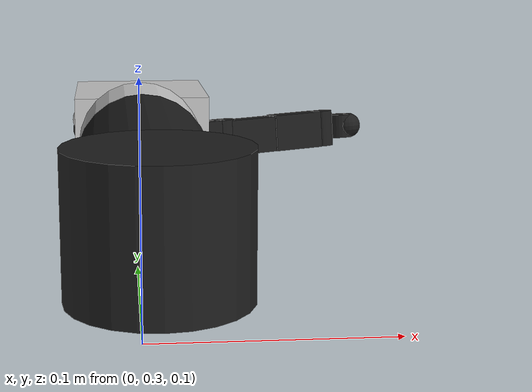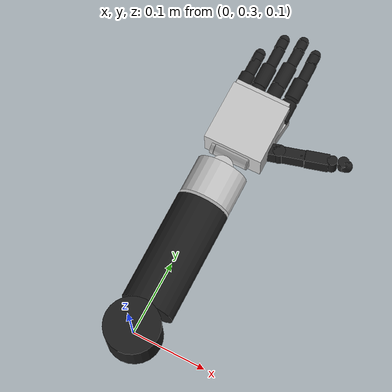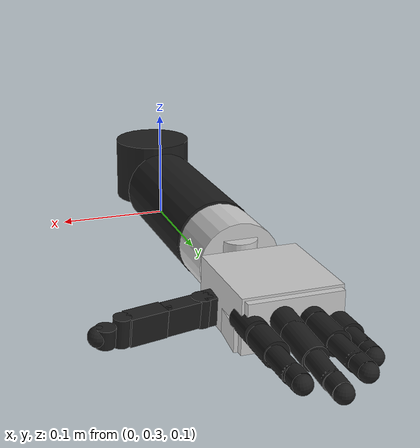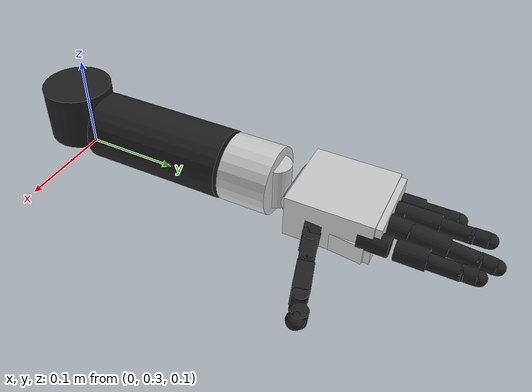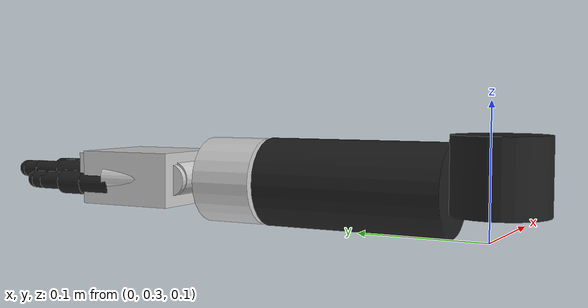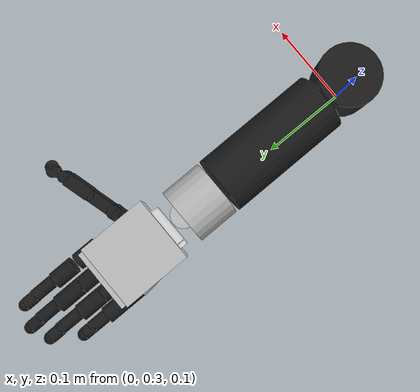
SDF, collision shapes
<sdf version='1.5'>
<model name="mpl_haptix_left_forearm">
  <plugin name="HaptixControlPlugin" filename="libHaptixControlPlugin.so">
    <update_rate>50</update_rate>
    <base_joint>elbow_dummy</base_joint>
    <base_link>forearm_dummy</base_link>
    <base_link_sensor_offset>0 0 0.07 3.14159 -1.570796 0</base_link_sensor_offset>
    <world_screen_location>0 -0.65 1.5 0 0 0</world_screen_location>
    <base_pid_pos cmd_max="10000.0" cmd_min="-10000.0" d="10.0" i="0" p="700.0"/>
    <base_pid_rot cmd_max="10000.0" cmd_min="-10000.0" d="10.0" i="0" p="800.0"/>
    <!-- order must match hxAPLJoints enumeration -->
    <joint id="0">elbow</joint>
    <joint id="1">wristy</joint>
    <joint id="2">wristx</joint>
    <joint id="3">wristz</joint>
    <joint id="4">thumb0</joint>
    <joint id="5">thumb1</joint>
    <joint id="6">thumb2</joint>
    <joint id="7">thumb3</joint>
    <joint id="8">index0</joint>
    <joint id="9">index1</joint>
    <joint id="10">index2</joint>
    <joint id="11">index3</joint>
    <joint id="12">middle1</joint>
    <joint id="13">middle2</joint>
    <joint id="14">middle3</joint>
    <joint id="15">ring0</joint>
    <joint id="16">ring1</joint>
    <joint id="17">ring2</joint>
    <joint id="18">ring3</joint>
    <joint id="19">pinky0</joint>
    <joint id="20">pinky1</joint>
    <joint id="21">pinky2</joint>
    <joint id="22">pinky3</joint>
    <pid cmd_max=" 500.0" cmd_min=" -500.0" d="0" i="0" id="0" p=" 1.0"/>
    <pid cmd_max=" 500.0" cmd_min=" -500.0" d="0" i="0" id="1" p=" 1.0"/>
    <pid cmd_max=" 500.0" cmd_min=" -500.0" d="0" i="0" id="2" p=" 1.0"/>
    <pid cmd_max=" 100.0" cmd_min=" -100.0" d="0" i="0" id="3" p=" 1.0"/>
    <pid cmd_max=" 100.0" cmd_min=" -100.0" d="0" i="0" id="4" p=" 1.0"/>
    <pid cmd_max=" 100.0" cmd_min=" -100.0" d="0" i="0" id="5" p=" 1.0"/>
    <pid cmd_max=" 100.0" cmd_min=" -100.0" d="0" i="0" id="6" p=" 1.0"/>
    <pid cmd_max=" 100.0" cmd_min=" -100.0" d="0" i="0" id="7" p=" 1.0"/>
    <pid cmd_max=" 100.0" cmd_min=" -100.0" d="0" i="0" id="8" p=" 1.0"/>
    <pid cmd_max=" 100.0" cmd_min=" -100.0" d="0" i="0" id="9" p=" 1.0"/>
    <pid cmd_max=" 100.0" cmd_min=" -100.0" d="0" i="0" id="10" p="1.0"/>
    <pid cmd_max=" 100.0" cmd_min=" -100.0" d="0" i="0" id="11" p="1.0"/>
    <pid cmd_max=" 100.0" cmd_min=" -100.0" d="0" i="0" id="12" p="1.0"/>
    <pid cmd_max=" 100.0" cmd_min=" -100.0" d="0" i="0" id="13" p="1.0"/>
    <pid cmd_max=" 100.0" cmd_min=" -100.0" d="0" i="0" id="14" p="1.0"/>
    <pid cmd_max=" 100.0" cmd_min=" -100.0" d="0" i="0" id="15" p="1.0"/>
    <pid cmd_max=" 100.0" cmd_min=" -100.0" d="0" i="0" id="16" p="1.0"/>
    <pid cmd_max=" 100.0" cmd_min=" -100.0" d="0" i="0" id="17" p="1.0"/>
    <pid cmd_max=" 100.0" cmd_min=" -100.0" d="0" i="0" id="18" p="1.0"/>
    <pid cmd_max=" 100.0" cmd_min=" -100.0" d="0" i="0" id="19" p="1.0"/>
    <pid cmd_max=" 100.0" cmd_min=" -100.0" d="0" i="0" id="20" p="1.0"/>
    <pid cmd_max=" 100.0" cmd_min=" -100.0" d="0" i="0" id="21" p="1.0"/>
    <pid cmd_max=" 100.0" cmd_min=" -100.0" d="0" i="0" id="22" p="1.0"/>

    <motor id="0" name="motor_elbow">
      <powered_motor_joint>elbow</powered_motor_joint>
      <!-- gear_ratio = motor angle / joint angle -->
      <!-- elbow motor torque unknown, guessing for now -->
      <motor_torque>10000</motor_torque>
      <gear_ratio>180.0</gear_ratio>
      <encoder_offset>0.0</encoder_offset>
    </motor>
    <motor id="1" name="motor_wristy">
      <powered_motor_joint>wristy</powered_motor_joint>
      <!-- gear_ratio = motor angle / joint angle -->
      <!-- wrist motor torque unknown, guessing for now -->
      <motor_torque>0.0382</motor_torque>
      <gear_ratio>180.0</gear_ratio>
      <encoder_offset>0.0</encoder_offset>
    </motor>
    <motor id="2" name="motor_wristx">
      <powered_motor_joint>wristx</powered_motor_joint>
      <!-- wrist motor torque unknown, guessing for now -->
      <motor_torque>0.003</motor_torque>
      <gear_ratio>180.0</gear_ratio>
      <encoder_offset>0.0</encoder_offset>
    </motor>
    <motor id="3" name="motor_wristz">
      <powered_motor_joint>wristz</powered_motor_joint>
      <!-- wrist motor torque unknown, guessing for now -->
      <motor_torque>0.0191</motor_torque>
      <gear_ratio>180.0</gear_ratio>
      <encoder_offset>0.0</encoder_offset>
    </motor>
    <motor id="4" name="motor_thumb0">
      <powered_motor_joint>thumb0</powered_motor_joint>
      <motor_torque>3.82e-3</motor_torque>
      <gear_ratio>352.0</gear_ratio>
      <encoder_offset>0.0</encoder_offset>
    </motor>
    <motor id="5" name="motor_thumb1">
      <powered_motor_joint>thumb1</powered_motor_joint>
      <motor_torque>2.0e-3</motor_torque>
      <gear_ratio>352.0</gear_ratio>
      <encoder_offset>0.0</encoder_offset>
    </motor>
    <motor id="6" name="motor_thumb2">
      <powered_motor_joint>thumb2</powered_motor_joint>
      <motor_torque>2.0e-3</motor_torque>
      <gear_ratio>352.0</gear_ratio>
      <encoder_offset>0.0</encoder_offset>
    </motor>
    <motor id="7" name="motor_thumb3">
      <powered_motor_joint>thumb3</powered_motor_joint>
      <motor_torque>1.0e-3</motor_torque>
      <gear_ratio>352.0</gear_ratio>
      <encoder_offset>0.0</encoder_offset>
    </motor>
    <motor id="8" name="motor_index0">
      <powered_motor_joint>index0</powered_motor_joint>
      <!--
        1MF gear ratio: 352, Allied Motion SL0500-S02-Z motor torque: 3.82e-3 Nm
        max differential joint torque = 1.50126 Nm
      -->
      <motor_torque>1.50e-3</motor_torque>
      <gear_ratio>352.0</gear_ratio>
      <encoder_offset>0</encoder_offset>
    </motor>
    <motor id="9" name="motor_index1">
      <!--
        1MF gear ratio: 383, Allied Motion SL0500-S02-Z motor torque: 3.82e-3 Nm
        max differential joint torque = 1.50126 Nm
        indexm: motor joint for index finger
      -->
      <powered_motor_joint>indexm</powered_motor_joint>
      <motor_torque>2.0e-3</motor_torque>
      <gear_ratio>393.0</gear_ratio>
      <encoder_offset>0.0</encoder_offset>
      <gearbox>
        <joint>index1</joint>
        <offset>0.174532925199</offset>
        <multiplier1>1.0</multiplier1>
        <multiplier2>0.833333</multiplier2>
      </gearbox>
      <gearbox>
        <joint>index2</joint>
        <offset>0.38397243543</offset>
        <multiplier1>0</multiplier1>
        <multiplier2>0.71875</multiplier2>
      </gearbox>
      <gearbox>
        <joint>index3</joint>
        <offset>0.38397243543</offset>
        <multiplier1>0</multiplier1>
        <multiplier2>0.69791667</multiplier2>
      </gearbox>
    </motor>
    <motor id="10" name="motor_middle1">
      <!--
        1MF gear ratio: 383, Allied Motion SL0500-S02-Z motor torque: 3.82e-3 Nm
        max differential joint torque = 1.50126 Nm
        middlem: motor joint for middle finger
      -->
      <powered_motor_joint>middlem</powered_motor_joint>
      <motor_torque>1.0e-3</motor_torque>
      <gear_ratio>393.0</gear_ratio>
      <encoder_offset>0.0</encoder_offset>
      <gearbox>
        <joint>middle1</joint>
        <offset>0.174532925199</offset>
        <multiplier1>1.0</multiplier1>
        <multiplier2>0.833333</multiplier2>
      </gearbox>
      <gearbox>
        <joint>middle2</joint>
        <offset>0.38397243543</offset>
        <multiplier1>0.0</multiplier1>
        <multiplier2>0.71875</multiplier2>
      </gearbox>
      <gearbox>
        <joint>middle3</joint>
        <offset>0.38397243543</offset>
        <multiplier1>0.0</multiplier1>
        <multiplier2>0.69791667</multiplier2>
      </gearbox>
    </motor>
    <motor id="11" name="motor_ring1">
      <!--
        1MF gear ratio: 383, Allied Motion SL0500-S02-Z motor torque: 3.82e-3 Nm
        max differential joint torque = 1.50126 Nm
        ringm: motor joint for ring finger
      -->
      <powered_motor_joint>ringm</powered_motor_joint>
      <motor_torque>0.5e-3</motor_torque>
      <gear_ratio>393.0</gear_ratio>
      <encoder_offset>0.0</encoder_offset>
      <gearbox>
        <joint>ring1</joint>
        <offset>0.174532925199</offset>
        <multiplier1>1.0</multiplier1>
        <multiplier2>0.833333</multiplier2>
      </gearbox>
      <gearbox>
        <joint>ring2</joint>
        <offset>0.38397243543</offset>
        <multiplier1>0.0</multiplier1>
        <multiplier2>0.71875</multiplier2>
      </gearbox>
      <gearbox>
        <joint>ring3</joint>
        <offset>0.38397243543</offset>
        <multiplier1>0.0</multiplier1>
        <multiplier2>0.69791667</multiplier2>
      </gearbox>
    </motor>
    <motor id="12" name="motor_pinky0">
      <powered_motor_joint>ring0</powered_motor_joint>
      <motor_torque>2.54e-3</motor_torque>
      <gear_ratio>352.0</gear_ratio>
      <encoder_offset>0.0</encoder_offset>
      <gearbox>
        <joint>pinky0</joint>
        <offset>0</offset>
        <multiplier1>1.0</multiplier1>
        <multiplier2>1.0</multiplier2>
      </gearbox>
    </motor>
    <motor id="13" name="motor_pinky1">
      <!--
        1MF gear ratio: 383, Allied Motion SL0500-S02-Z motor torque: 3.82e-3 Nm
        max differential joint torque = 1.50126 Nm
        pinkym: motor joint for pinky finger
      -->
      <powered_motor_joint>pinkym</powered_motor_joint>
      <motor_torque>0.5e-3</motor_torque>
      <gear_ratio>393.0</gear_ratio>
      <encoder_offset>0.0</encoder_offset>
      <gearbox>
        <joint>pinky1</joint>
        <offset>0.174532925199</offset>
        <multiplier1>1.0</multiplier1>
        <multiplier2>0.833333</multiplier2>motorInfo.gearRati
      </gearbox>
      <gearbox>
        <joint>pinky2</joint>
        <offset>0.38397243543</offset>
        <multiplier1>0.0</multiplier1>
        <multiplier2>0.71875</multiplier2>
      </gearbox>
      <gearbox>
        <joint>pinky3</joint>
        <offset>0.38397243543</offset>
        <multiplier1>0.0</multiplier1>
        <multiplier2>0.69791667</multiplier2>
      </gearbox>
    </motor>
    <contactSensor id="0">palm0_contact_sensor</contactSensor>
    <contactSensor id="1">palm1_contact_sensor</contactSensor>
    <contactSensor id="2">palmEdge_contact_sensor</contactSensor>
    <contactSensor id="3">handTop_contact_sensor</contactSensor>
    <contactSensor id="4">thumb1_contact_sensor</contactSensor>
    <contactSensor id="5">thumb2_contact_sensor</contactSensor>
    <contactSensor id="6">thumb3_contact_sensor</contactSensor>
    <contactSensor id="7">index1_contact_sensor</contactSensor>
    <contactSensor id="8">index2_contact_sensor</contactSensor>
    <contactSensor id="9">index3_contact_sensor</contactSensor>
    <contactSensor id="10">middle1_contact_sensor</contactSensor>
    <contactSensor id="11">middle2_contact_sensor</contactSensor>
    <contactSensor id="12">middle3_contact_sensor</contactSensor>
    <contactSensor id="13">ring1_contact_sensor</contactSensor>
    <contactSensor id="14">ring2_contact_sensor</contactSensor>
    <contactSensor id="15">ring3_contact_sensor</contactSensor>
    <contactSensor id="16">pinky1_contact_sensor</contactSensor>
    <contactSensor id="17">pinky2_contact_sensor</contactSensor>
    <contactSensor id="18">pinky3_contact_sensor</contactSensor>
    <imuSensor id="0">thumb3_imu_sensor</imuSensor>
    <imuSensor id="1">index3_imu_sensor</imuSensor>
    <imuSensor id="2">middle3_imu_sensor</imuSensor>
    <imuSensor id="3">ring3_imu_sensor</imuSensor>
    <imuSensor id="4">pinky3_imu_sensor</imuSensor>
    <!-- These grasp postures are based on information from APL -->
    <grasp name="2Pinch">
        <point>
          <inputs>0.20000   0.20000   0.20000   0.20000   0.20000   0.20000   0.20000   0.20000   0.20000   0.20000   0.20000   0.20000   0.20000</inputs>
          <motors>0.00000  0.00000  0.00000   517.44000     0.00000     0.00000    0.00000     0.00000     0.00000     0.00000     0.00000     0.00000    0.00000</motors>
        </point>
        <point>
          <inputs>1.00000   1.00000   1.00000   1.00000   1.00000   1.00000   1.00000   1.00000   1.00000   1.00000   1.00000   1.00000   1.00000</inputs>
          <motors>0.00000  0.00000  0.00000   517.44000   355.23136   152.06048   60.82560     0.00000   441.69270     0.00000     0.00000     0.00000    0.00000</motors>
        </point>
    </grasp>
    <grasp name="Cylindrical">
        <point>
          <inputs>0.20000   0.20000   0.20000   0.20000   0.20000   0.20000   0.20000   0.20000   0.20000   0.20000   0.20000   0.20000   0.20000</inputs>
          <motors>0.00000  0.00000  0.00000   633.60000     0.00000     0.00000    0.00000     0.00000     0.00000     0.00000     0.00000     0.00000    0.00000</motors>
        </point>
        <point>
          <inputs>1.00000   1.00000   1.00000   1.00000   1.00000   1.00000   1.00000   1.00000   1.00000   1.00000   1.00000   1.00000   1.00000</inputs>
          <motors>0.00000  0.00000  0.00000   633.60000    17.60000   264.00000  264.00000  -105.60000   445.85850   469.43850   469.43850     0.00000  445.85850</motors>
        </point>
    </grasp>
    <grasp name="Spherical">
        <point>
          <inputs>0.20000   0.20000   0.20000   0.20000   0.20000   0.20000   0.20000   0.20000   0.20000   0.20000   0.20000   0.20000   0.20000</inputs>
          <motors>0.00000  0.00000  0.00000   633.60000     0.00000     0.00000    0.00000  -105.60000     0.00000     0.00000     0.00000   122.88320    0.00000</motors>
        </point>
        <point>
          <inputs>1.00000   1.00000   1.00000   1.00000   1.00000   1.00000   1.00000   1.00000   1.00000   1.00000   1.00000   1.00000   1.00000</inputs>
          <motors>0.00000  0.00000  0.00000   675.80480   184.30720   307.19040 -122.88320  -105.60000   521.26734   438.97314   480.14382   122.88320  562.43802</motors>
        </point>
    </grasp>
    <grasp name="ThreeFingerPinch">
     0.00000     0.00000     0.00000   686.52320   355.23136   152.06048     60.82560     0.00000   441.69270   492.05565   394.53270     0.00000
    </grasp>
    <grasp name="FinePinch(American)">
     0.00000     0.00000     0.00000   491.49760   307.19040   184.30720   -122.88320     0.00000   480.14382   809.36778   809.36778     562.43802
    </grasp>
    <grasp name="FinePinch(British)">
     0.00000     0.00000     0.00000   494.29600   326.16672   109.48256    114.19584   -17.60000   407.96151   397.05969   -74.01369     0.00000
    </grasp>
    <grasp name="Palmar(Tray)">
     0.00000     0.00000     0.00000   552.92160   491.49760   245.73120   -122.88320     0.00000    68.57850    68.57850    68.57850     562.43802
    </grasp>
    <grasp name="Hook">
     0.00000     0.00000     0.00000     0.00000   368.61440    92.15360   -122.88320     0.00000   644.73222   644.73222   644.73222     562.43802
    </grasp>
  </plugin>

  <!-- Model SDF copied from gazebo_models -->
  <joint name='elbow_dummy' type='revolute'>
    <child>forearm_dummy</child>
    <parent>world</parent>
    <axis>
      <xyz>0 0 1.0</xyz>
      <limit>
        <lower>0</lower>
        <upper>0</upper>
        <effort>10000</effort>
        <velocity>-1</velocity>
      </limit>
      <dynamics>
        <damping>2</damping>
        <friction>0</friction>
        <spring_reference>0</spring_reference>
        <spring_stiffness>0</spring_stiffness>
      </dynamics>
      <use_parent_model_frame>1</use_parent_model_frame>
    </axis>
    <physics>
      <provide_feedback>1</provide_feedback>
      <ode>
        <provide_feedback>1</provide_feedback>
        <implicit_spring_damper>1</implicit_spring_damper>
        <cfm_damping>1</cfm_damping>
        <limit>
          <cfm>0.01</cfm>
          <erp>0</erp>
        </limit>
      </ode>
    </physics>
  </joint>
  <link name='forearm_dummy'>
    <gravity>0</gravity>
    <pose>0.00660504 -0.294573 0.119123 -1.21334e-13 2.77556e-17 -0.0115373</pose>
    <inertial>
      <pose>-0.000589428 -0.0733139 0.0215526 0 0 0</pose>
      <mass>0.0997005</mass>
      <inertia>
        <ixx>0.0004998</ixx>
        <ixy>-5.83136e-06</ixy>
        <ixz>3.56083e-07</ixz>
        <iyy>0.00010215</iyy>
        <iyz>3.76069e-05</iyz>
        <izz>0.000498862</izz>
      </inertia>
    </inertial>
  </link>

  <joint name='elbow' type='revolute'>
    <child>forearm</child>
    <parent>forearm_dummy</parent>
    <axis>
      <xyz>0 0 -1.0</xyz>
      <limit>
        <lower>0</lower>
        <upper>1.57</upper>
        <effort>-1</effort>
        <velocity>-1</velocity>
      </limit>
      <dynamics>
        <damping>0.66</damping>
        <friction>0</friction>
        <spring_reference>0</spring_reference>
        <spring_stiffness>0</spring_stiffness>
      </dynamics>
      <use_parent_model_frame>1</use_parent_model_frame>
    </axis>
    <physics>
      <provide_feedback>1</provide_feedback>
      <ode>
        <provide_feedback>1</provide_feedback>
        <implicit_spring_damper>1</implicit_spring_damper>
        <cfm_damping>1</cfm_damping>
        <limit>
          <cfm>0.01</cfm>
          <erp>0</erp>
        </limit>
      </ode>
    </physics>
  </joint>
  <link name='forearm'>
<gravity>1</gravity>
    <pose>0.00660504 0.294573 0.119123 1.21334e-13 2.77556e-17 0.0115373</pose>
    <inertial>
      <pose>-0.000589428 0.0733139 0.0215526 0 0 0</pose>
      <mass>0.0997005</mass>
      <inertia>
        <ixx>0.0004998</ixx>
        <ixy>-5.83136e-06</ixy>
        <ixz>3.56083e-07</ixz>
        <iyy>0.00010215</iyy>
        <iyz>3.76069e-05</iyz>
        <izz>0.000498862</izz>
      </inertia>
    </inertial>
    <collision name='collision'>
      <pose>0 0 0.02855 0 0 0</pose>
      <geometry>
        <cylinder>
          <radius>0.03567</radius>
          <length>0.0571</length>
        </cylinder>
      </geometry>
      <surface>
        <contact>
          <ode>
            <kp>100000</kp>
            <kd>100</kd>
            <max_vel>0.1</max_vel>
            <min_depth>0.0015</min_depth>
          </ode>
        </contact>
        <friction>
          <ode>
            <mu>1</mu>
            <mu2>1</mu2>
          </ode>
        </friction>
      </surface>
    </collision>
    <collision name='collision_1'>
      <pose>0 0.10745 0.016 -1.5707 0 0</pose>
      <geometry>
        <cylinder>
          <radius>0.035</radius>
          <length>0.148</length>
        </cylinder>
      </geometry>
      <surface>
        <contact>
          <ode>
            <kp>100000</kp>
            <kd>100</kd>
            <max_vel>0.1</max_vel>
            <min_depth>0.0015</min_depth>
          </ode>
        </contact>
        <friction>
          <ode>
            <mu>1</mu>
            <mu2>1</mu2>
          </ode>
        </friction>
      </surface>
    </collision>
    <visual name='visual'>
      <geometry>
        <mesh>
          <uri>model://mpl_haptix_left_forearm/meshes/forearm.stl</uri>
        </mesh>
      </geometry>
      <material>
        <script>
          <name>Gazebo/FlatBlack</name>
        </script>
      </material>
    </visual>
  </link>

  <link name='wristy'>
    <gravity>0</gravity> <!-- REMEMBER TO TURN ME BACK ON -->
    <pose>0.00449937 0.479995 0.135123 1.2164e-13 1.09079e-14 0.0115373</pose>
    <inertial>
      <pose>-7.08369e-05 0.0217787 -0.000286168 0 0 0</pose>
      <mass>0.0272932</mass>
      <inertia>
        <ixx>1.77029e-05</ixx>
        <ixy>7.89061e-09</ixy>
        <ixz>4.33867e-09</ixz>
        <iyy>2.46772e-05</iyy>
        <iyz>1.77331e-07</iyz>
        <izz>1.7112e-05</izz>
      </inertia>
    </inertial>
    <collision name='collision'>
      <pose>0 0.025 0 -1.5707 0 0</pose>
      <geometry>
        <cylinder>
          <radius>0.03447</radius>
          <length>0.05</length>
        </cylinder>
      </geometry>
      <surface>
        <contact>
          <ode>
            <kp>100000</kp>
            <kd>100</kd>
            <max_vel>0.1</max_vel>
            <min_depth>0.0015</min_depth>
          </ode>
        </contact>
        <friction>
          <ode>
            <mu>1</mu>
            <mu2>1</mu2>
          </ode>
        </friction>
      </surface>
    </collision>
    <visual name='visual'>
      <geometry>
        <mesh>
          <uri>model://mpl_haptix_left_forearm/meshes/wristy.stl</uri>
        </mesh>
      </geometry>
      <material>
        <ambient>0.2 0.2 0.2 1</ambient>
        <diffuse>0.8 0.8 0.8 1</diffuse>
        <specular>0.9 0.9 0.9 1</specular>
      </material>
    </visual>
  </link>
  <joint name='wristy' type='revolute'>
    <child>wristy</child>
    <parent>forearm</parent>
    <axis>
      <xyz>-0.011537 0.999933 1.2164e-13</xyz>
      <limit>
        <lower>-1.57</lower>
        <upper>1.57</upper>
        <effort>10000</effort>
        <velocity>-1</velocity>
      </limit>
      <dynamics>
        <damping>2</damping>
        <friction>0</friction>
        <spring_reference>0</spring_reference>
        <spring_stiffness>0</spring_stiffness>
      </dynamics>
      <use_parent_model_frame>1</use_parent_model_frame>
    </axis>
    <physics>
      <provide_feedback>1</provide_feedback>
      <ode>
        <implicit_spring_damper>1</implicit_spring_damper>
        <cfm_damping>1</cfm_damping>
        <limit>
          <cfm>0.01</cfm>
          <erp>0.1</erp>
        </limit>
      </ode>
    </physics>
  </joint>

  <link name='wristx'>
    <gravity>0</gravity> <!-- REMEMBER TO TURN ME BACK ON -->
    <pose>0.003916 0.527636 0.137161 1.18962e-13 1.21847e-14 0.0115373</pose>
    <inertial>
      <pose>0.00139174 0.00975189 -0.00252668 0 0 0</pose>
      <mass>0.010691</mass>
      <inertia>
        <ixx>3.27995e-06</ixx>
        <ixy>-1.50151e-07</ixy>
        <ixz>5.11904e-09</ixz>
        <iyy>4.22942e-06</iyy>
        <iyz>-4.20007e-08</iyz>
        <izz>5.04229e-06</izz>
      </inertia>
    </inertial>
    <collision name='collision'>
      <pose>0 0 -0.00314 0 0 0</pose>
      <geometry>
        <cylinder>
          <radius>0.01473</radius>
          <length>0.04478</length>
        </cylinder>
      </geometry>
      <surface>
        <contact>
          <ode>
            <kp>100000</kp>
            <kd>100</kd>
            <max_vel>0.1</max_vel>
            <min_depth>0.0015</min_depth>
          </ode>
        </contact>
        <friction>
          <ode>
            <mu>1</mu>
            <mu2>1</mu2>
          </ode>
        </friction>
      </surface>
    </collision>
    <collision name='collision_1'>
      <pose>0.02360 0.02969 -0.00240 0 1.5707 0</pose>
      <geometry>
        <cylinder>
          <radius>0.013175</radius>
          <length>0.005</length>
        </cylinder>
      </geometry>
      <surface>
        <contact>
          <ode>
            <kp>100000</kp>
            <kd>100</kd>
            <max_vel>0.1</max_vel>
            <min_depth>0.0015</min_depth>
          </ode>
        </contact>
        <friction>
          <ode>
            <mu>1</mu>
            <mu2>1</mu2>
          </ode>
        </friction>
      </surface>
    </collision>
    <collision name='collision_2'>
      <pose>-0.02360 0.02969 -0.00240 0 1.5707 0</pose>
      <geometry>
        <cylinder>
          <radius>0.013175</radius>
          <length>0.005</length>
        </cylinder>
      </geometry>
      <surface>
        <contact>
          <ode>
            <kp>100000</kp>
            <kd>100</kd>
            <max_vel>0.1</max_vel>
            <min_depth>0.0015</min_depth>
          </ode>
        </contact>
        <friction>
          <ode>
            <mu>1</mu>
            <mu2>1</mu2>
          </ode>
        </friction>
      </surface>
    </collision>
    <visual name='visual'>
      <geometry>
        <mesh>
          <uri>model://mpl_haptix_left_forearm/meshes/wristx.stl</uri>
        </mesh>
      </geometry>
      <material>
        <ambient>0.2 0.2 0.2 1</ambient>
        <diffuse>0.8 0.8 0.8 1</diffuse>
        <specular>0.9 0.9 0.9 1</specular>
      </material>
    </visual>
  </link>
  <joint name='wristx' type='revolute'>
    <child>wristx</child>
    <parent>wristy</parent>
    <axis>
      <xyz>1.35564e-14 -1.18814e-13 1</xyz>
      <limit>
        <lower>-0.261</lower>
        <upper>0.785</upper>
        <effort>10000</effort>
        <velocity>-1</velocity>
      </limit>
      <dynamics>
        <damping>0.1</damping>
        <friction>0</friction>
        <spring_reference>0</spring_reference>
        <spring_stiffness>0</spring_stiffness>
      </dynamics>
      <use_parent_model_frame>1</use_parent_model_frame>
    </axis>
    <physics>
      <provide_feedback>1</provide_feedback>
      <ode>
        <implicit_spring_damper>1</implicit_spring_damper>
        <cfm_damping>1</cfm_damping>
        <limit>
          <cfm>0.01</cfm>
          <erp>0.1</erp>
        </limit>
      </ode>
    </physics>
  </joint>

  <link name='wristz'>
    <gravity>0</gravity> <!-- REMEMBER TO TURN ME BACK ON -->
    <pose>0.00375708 0.557636 0.135067 2.87105e-13 1.42109e-14 0.0115373</pose>
    <inertial>
      <pose>0.00368152 0.0358755 0.00265927 0 0 0</pose>
      <mass>0.125889</mass>
      <inertia>
        <ixx>8.18077e-05</ixx>
        <ixy>-9.44149e-06</ixy>
        <ixz>3.88366e-06</ixz>
        <iyy>9.81482e-05</iyy>
        <iyz>-4.84151e-08</iyz>
        <izz>0.000131783</izz>
      </inertia>
    </inertial>
    <collision name='collision'>
      <pose>0.00207 0.00047 0.00046 -1.5707 0 -1.5707</pose>
      <geometry>
        <cylinder>
          <radius>0.01411</radius>
          <length>0.04482</length>
        </cylinder>
      </geometry>
      <surface>
        <contact>
          <ode>
            <kp>100000</kp>
            <kd>100</kd>
            <max_vel>0.1</max_vel>
            <min_depth>0.0015</min_depth>
          </ode>
        </contact>
        <friction>
          <ode>
            <mu>1</mu>
            <mu2>1</mu2>
          </ode>
        </friction>
      </surface>
    </collision>
    <collision name='collision_palm'>
      <pose>0.002 0.03739 0 0 0 0</pose>
      <geometry>
        <box>
          <size>0.07928 0.08316 0.04402</size>
        </box>
      </geometry>
      <surface>
        <contact>
          <ode>
            <kp>100000</kp>
            <kd>100</kd>
            <max_vel>0.1</max_vel>
            <min_depth>0.0015</min_depth>
          </ode>
        </contact>
        <friction>
          <ode>
            <mu>1</mu>
            <mu2>1</mu2>
          </ode>
        </friction>
      </surface>
    </collision>
    <collision name="palmEdge">
      <pose>-0.028 0.03 0 -1.57 0 0.1</pose>
      <geometry>
        <cylinder>
          <radius>0.01</radius>
          <length>0.060</length>
        </cylinder>
      </geometry>
      <surface>
        <contact>
          <ode>
            <kp>100000</kp>
            <kd>100</kd>
            <max_vel>0.1</max_vel>
            <min_depth>0.0015</min_depth>
          </ode>
        </contact>
        <friction>
          <ode>
            <mu>1</mu>
            <mu2>1</mu2>
          </ode>
        </friction>
      </surface>
    </collision>
   <!-- Dorsal surface (top) -->
    <collision name="handTop">
      <pose>0.002 0.045 0.01 0 0 0</pose>
      <geometry>
        <box>
          <size>0.075 0.08 0.02</size>
        </box>
      </geometry>
      <surface>
        <contact>
          <ode>
            <kp>100000</kp>
            <kd>100</kd>
            <max_vel>0.1</max_vel>
            <min_depth>0.0015</min_depth>
          </ode>
        </contact>
        <friction>
          <ode>
            <mu>1</mu>
            <mu2>1</mu2>
          </ode>
        </friction>
      </surface>
    </collision>
    <!-- Palm 0 (closer to thumb) -->
    <collision name="palm0">
      <pose>0.023 0.04 -0.012 0 0 -0.1</pose>
      <geometry>
        <box>
          <size>0.037 0.07 0.02</size>
        </box>
      </geometry>
      <surface>
        <contact>
          <ode>
            <kp>100000</kp>
            <kd>100</kd>
            <max_vel>0.1</max_vel>
            <min_depth>0.0015</min_depth>
          </ode>
        </contact>
        <friction>
          <ode>
            <mu>1</mu>
            <mu2>1</mu2>
          </ode>
        </friction>
      </surface>
    </collision>
    <!-- Palm 1 (closer to pinky) -->
    <collision name="palm1">
      <pose>-0.018 0.04 -0.012 0 0 0</pose>
      <geometry>
        <box>
          <size>0.037 0.07 0.02</size>
        </box>
      </geometry>
      <surface>
        <contact>
          <ode>
            <kp>100000</kp>
            <kd>100</kd>
            <max_vel>0.1</max_vel>
            <min_depth>0.0015</min_depth>
          </ode>
        </contact>
        <friction>
          <ode>
            <mu>1</mu>
            <mu2>1</mu2>
          </ode>
        </friction>
      </surface>
    </collision>
    <visual name='visual'>
      <geometry>
        <mesh>
          <uri>model://mpl_haptix_left_forearm/meshes/wristz.stl</uri>
        </mesh>
      </geometry>
      <material>
        <ambient>0.2 0.2 0.2 1</ambient>
        <diffuse>0.8 0.8 0.8 1</diffuse>
        <specular>0.9 0.9 0.9 1</specular>
      </material>
    </visual>
    <visual name='visual_palm'>
      <pose>0.025625 0 0 -1.7427e-13 8.3267e-17 3.1876e-16</pose>
      <geometry>
        <mesh>
          <uri>model://mpl_haptix_left_forearm/meshes/palm.stl</uri>
        </mesh>
      </geometry>
      <material>
        <script>
          <name>Gazebo/FlatBlack</name>
        </script>
      </material>
    </visual>
    <sensor name='palm0_contact_sensor' type='contact'>
      <always_on>1</always_on>
      <contact>
        <collision>palm0</collision>
      </contact>
    </sensor>
    <sensor name='palm1_contact_sensor' type='contact'>
      <always_on>1</always_on>
      <contact>
        <collision>palm1</collision>
      </contact>
    </sensor>
    <sensor name='palmEdge_contact_sensor' type='contact'>
      <always_on>1</always_on>
      <contact>
        <collision>palmEdge</collision>
      </contact>
    </sensor>
    <sensor name='handTop_contact_sensor' type='contact'>
      <always_on>1</always_on>
      <contact>
        <collision>handTop</collision>
      </contact>
    </sensor>
  </link>
  <joint name='wristz' type='revolute'>
    <child>wristz</child>
    <parent>wristx</parent>
    <axis>
      <xyz>-0.999933 -0.011537 1.42109e-14</xyz>
      <limit>
        <lower>-1.04</lower>
        <upper>1.04</upper>
        <effort>10000</effort>
        <velocity>-1</velocity>
      </limit>
      <dynamics>
        <damping>2</damping>
        <friction>0</friction>
        <spring_reference>0</spring_reference>
        <spring_stiffness>0</spring_stiffness>
      </dynamics>
      <use_parent_model_frame>1</use_parent_model_frame>
    </axis>
    <physics>
      <provide_feedback>1</provide_feedback>
      <ode>
        <implicit_spring_damper>1</implicit_spring_damper>
        <cfm_damping>1</cfm_damping>
        <limit>
          <cfm>0.01</cfm>
          <erp>0.1</erp>
        </limit>
      </ode>
    </physics>
  </joint>

  <link name='index0'>
    <gravity>1</gravity> <!-- REMEMBER TO TURN ME BACK ON -->
    <pose>0.0384854 0.623842 0.136079 1.14726e-13 0.174533 0.0115373</pose>
    <inertial>
      <pose>-0.000142572 0.00548494 0.000206145 0 0 0</pose>
      <mass>0.00295579</mass>
      <inertia>
        <ixx>4.22375e-07</ixx>
        <ixy>4.23313e-09</ixy>
        <ixz>5.00708e-10</ixz>
        <iyy>1.94048e-07</iyy>
        <iyz>-4.58697e-09</iyz>
        <izz>4.02188e-07</izz>
      </inertia>
    </inertial>
    <collision name='collision'>
      <pose>0 0.01339 0 -1.5707 0 0</pose>
      <geometry>
        <cylinder>
          <length>0.028</length>
          <radius>0.01</radius>
        </cylinder>
      </geometry>
      <surface>
        <contact>
          <ode>
            <kp>100000</kp>
            <kd>100</kd>
            <max_vel>0.1</max_vel>
            <min_depth>0.0015</min_depth>
          </ode>
        </contact>
        <friction>
          <ode>
            <mu>1</mu>
            <mu2>1</mu2>
          </ode>
        </friction>
      </surface>
    </collision>
    <visual name='visual'>
      <geometry>
        <mesh>
          <uri>model://mpl_haptix_left_forearm/meshes/index0.stl</uri>
        </mesh>
      </geometry>
      <material>
        <script>
          <name>Gazebo/FlatBlack</name>
        </script>
      </material>
    </visual>
  </link>
  <joint name='index0' type='revolute'>
    <child>index0</child>
    <parent>wristz</parent>
    <axis>
      <xyz>0.173637 0.00200338 0.984808</xyz>
      <limit>
        <lower>-0.345</lower>
        <upper>0</upper>
        <effort>10000</effort>
        <velocity>-1</velocity>
      </limit>
      <dynamics>
        <damping>1</damping>
        <friction>0</friction>
        <spring_reference>0</spring_reference>
        <spring_stiffness>0</spring_stiffness>
      </dynamics>
      <use_parent_model_frame>1</use_parent_model_frame>
    </axis>
    <physics>
      <provide_feedback>1</provide_feedback>
      <ode>
        <implicit_spring_damper>1</implicit_spring_damper>
        <cfm_damping>1</cfm_damping>
        <limit>
          <cfm>0.01</cfm>
          <erp>0.1</erp>
        </limit>
      </ode>
    </physics>
  </joint>

  <link name='index1'>
    <gravity>1</gravity> <!-- REMEMBER TO TURN ME BACK ON -->

    <pose>0.0383394 0.641841 0.136068 1.1474e-13 0.174533 0.0115373</pose>
    <inertial>
      <pose>0.000406487 0.0213125 0.000655609 0 0 0</pose>
      <mass>0.00478235</mass>
      <inertia>
        <ixx>8.18593e-07</ixx>
        <ixy>-1.2874e-09</ixy>
        <ixz>1.78664e-10</ixz>
        <iyy>3.06547e-07</iyy>
        <iyz>-1.18998e-08</iyz>
        <izz>7.95406e-07</izz>
      </inertia>
    </inertial>
    <collision name='collision'>
      <pose>0 0.02782 0 -1.5707 0 0</pose>
      <geometry>
        <cylinder>
          <radius>0.01</radius>
          <length>0.02781</length>
        </cylinder>
      </geometry>
      <surface>
        <contact>
          <ode>
            <kp>100000</kp>
            <kd>100</kd>
            <max_vel>0.1</max_vel>
            <min_depth>0.0015</min_depth>
          </ode>
        </contact>
        <friction>
          <ode>
            <mu>1</mu>
            <mu2>1</mu2>
          </ode>
        </friction>
      </surface>
    </collision>
    <visual name='visual'>
      <geometry>
        <mesh>
          <uri>model://mpl_haptix_left_forearm/meshes/index1.stl</uri>
        </mesh>
      </geometry>
      <material>
        <script>
          <name>Gazebo/FlatBlack</name>
        </script>
      </material>
    </visual>
    <sensor name='index1_contact_sensor' type='contact'>
      <always_on>1</always_on>
      <contact>
        <collision>collision</collision>
      </contact>
    </sensor>
  </link>
  <joint name='index1' type='revolute'>
    <child>index1</child>
    <parent>index0</parent>
    <axis>
      <xyz>-0.984742 -0.0113618 0.173648</xyz>
      <limit>
        <lower>-0.785</lower>
        <upper>1.57</upper>
        <effort>10000</effort>
        <velocity>-1</velocity>
      </limit>
      <dynamics>
        <damping>0.5</damping>
        <friction>0</friction>
        <spring_reference>0</spring_reference>
        <spring_stiffness>0</spring_stiffness>
      </dynamics>
      <use_parent_model_frame>1</use_parent_model_frame>
    </axis>
    <physics>
      <provide_feedback>1</provide_feedback>
      <ode>
        <implicit_spring_damper>1</implicit_spring_damper>
        <cfm_damping>1</cfm_damping>
        <limit>
          <cfm>0.01</cfm>
          <erp>0.1</erp>
        </limit>
      </ode>
    </physics>
  </joint>

  <link name='index2'>
    <gravity>1</gravity> <!-- REMEMBER TO TURN ME BACK ON -->

    <pose>0.0389938 0.685352 0.136372 1.1445e-13 0.174533 0.0115373</pose>
    <inertial>
      <pose>-0.000841462 0.012689 0.000572665 0 0 0</pose>
      <mass>0.00344764</mass>
      <inertia>
        <ixx>3.63785e-07</ixx>
        <ixy>-6.41791e-09</ixy>
        <ixz>7.97765e-10</ixz>
        <iyy>1.07105e-07</iyy>
        <iyz>2.03273e-08</iyz>
        <izz>3.57435e-07</izz>
      </inertia>
    </inertial>
    <collision name='collision'>
      <pose>0 0.01152 0 -1.5707 0 0</pose>
      <geometry>
        <cylinder>
          <length>0.029</length>
          <radius>0.0075</radius>
        </cylinder>
      </geometry>
      <surface>
        <contact>
          <ode>
            <kp>100000</kp>
            <kd>100</kd>
            <max_vel>0.1</max_vel>
            <min_depth>0.0015</min_depth>
          </ode>
        </contact>
        <friction>
          <ode>
            <mu>1</mu>
            <mu2>1</mu2>
          </ode>
        </friction>
      </surface>
    </collision>
    <collision name='collision_1'>
      <pose>0 0.02502 0 0 0 0</pose>
      <geometry>
        <sphere>
          <radius>0.0075</radius>
        </sphere>
      </geometry>
      <surface>
        <contact>
          <ode>
            <kp>100000</kp>
            <kd>100</kd>
            <max_vel>0.1</max_vel>
            <min_depth>0.0015</min_depth>
          </ode>
        </contact>
        <friction>
          <ode>
            <mu>1</mu>
            <mu2>1</mu2>
          </ode>
        </friction>
      </surface>
    </collision>
    <visual name='visual'>
      <geometry>
        <mesh>
          <uri>model://mpl_haptix_left_forearm/meshes/index2.stl</uri>
        </mesh>
      </geometry>
      <material>
        <script>
          <name>Gazebo/FlatBlack</name>
        </script>
      </material>
    </visual>
    <sensor name='index2_contact_sensor' type='contact'>
      <always_on>1</always_on>
      <contact>
        <collision>collision</collision>
        <collision>collision_1</collision>
      </contact>
    </sensor>
  </link>
  <joint name='index2' type='revolute'>
    <child>index2</child>
    <parent>index1</parent>
    <axis>
      <xyz>-0.984742 -0.0113618 0.173648</xyz>
      <limit>
        <lower>0</lower>
        <upper>1.72</upper>
        <effort>10000</effort>
        <velocity>-1</velocity>
      </limit>
      <dynamics>
        <damping>0.25</damping>
        <friction>0</friction>
        <spring_reference>0</spring_reference>
        <spring_stiffness>0</spring_stiffness>
      </dynamics>
      <use_parent_model_frame>1</use_parent_model_frame>
    </axis>
    <physics>
      <provide_feedback>1</provide_feedback>
      <ode>
        <implicit_spring_damper>1</implicit_spring_damper>
        <cfm_damping>1</cfm_damping>
        <limit>
          <cfm>0.01</cfm>
          <erp>0.1</erp>
        </limit>
      </ode>
    </physics>
  </joint>

  <link name='index3'>
    <gravity>1</gravity> <!-- REMEMBER TO TURN ME BACK ON -->

    <self_collide>true</self_collide>
    <pose>0.0380858 0.709843 0.136482 1.15476e-13 0.174533 0.0115373</pose>
    <inertial>
      <pose>4.32004e-05 0.0125318 0.000903476 0 0 0</pose>
      <mass>0.00274415</mass>
      <inertia>
        <ixx>1.09202e-07</ixx>
        <ixy>-3.99165e-12</ixy>
        <ixz>-5.84792e-12</ixz>
        <iyy>7.79728e-08</iyy>
        <iyz>2.77966e-09</iyz>
        <izz>1.19449e-07</izz>
      </inertia>
    </inertial>
    <collision name='collision'>
      <pose>0 0.00688 0.0001 -1.5707 0 0</pose>
      <geometry>
        <cylinder>
          <length>0.01376</length>
          <radius>0.0074</radius>
        </cylinder>
      </geometry>
      <surface>
        <contact>
          <ode>
            <kp>100000</kp>
            <kd>100</kd>
            <max_vel>0.1</max_vel>
            <min_depth>0.0015</min_depth>
          </ode>
        </contact>
        <friction>
          <ode>
            <mu>1</mu>
            <mu2>1</mu2>
          </ode>
        </friction>
      </surface>
    </collision>
    <collision name='collision_1'>
      <pose>0 0.015 0.0001 0 0 0</pose>
      <geometry>
        <sphere>
          <radius>0.0072</radius>
        </sphere>
      </geometry>
      <surface>
        <contact>
          <ode>
            <kp>100000</kp>
            <kd>100</kd>
            <max_vel>0.1</max_vel>
            <min_depth>0.0015</min_depth>
          </ode>
        </contact>
        <friction>
          <ode>
            <mu>1</mu>
            <mu2>1</mu2>
          </ode>
        </friction>
      </surface>
    </collision>
    <visual name='visual'>
      <geometry>
        <mesh>
          <uri>model://mpl_haptix_left_forearm/meshes/index3.stl</uri>
        </mesh>
      </geometry>
      <material>
        <script>
          <name>Gazebo/FlatBlack</name>
        </script>
      </material>
    </visual>
    <sensor name='index3_contact_sensor' type='contact'>
      <always_on>1</always_on>
      <contact>
        <collision>collision</collision>
        <collision>collision_1</collision>
      </contact>
    </sensor>
    <sensor name='index3_imu_sensor' type='imu'>
      <pose>0 0 0  1.570796 -1.570796 0</pose>
      <always_on>1</always_on>
      <update_rate>1000</update_rate>
      <imu>
        <noise>
          <type>gaussian</type>
          <rate>
            <mean>0</mean>
            <stddev>0.0002</stddev>
            <bias_mean>7.5e-06</bias_mean>
            <bias_stddev>8e-07</bias_stddev>
          </rate>
          <accel>
            <mean>0</mean>
            <stddev>0.017</stddev>
            <bias_mean>0.1</bias_mean>
            <bias_stddev>0.001</bias_stddev>
          </accel>
        </noise>
      </imu>
    </sensor>
  </link>
  <joint name='index3' type='revolute'>
    <child>index3</child>
    <parent>index2</parent>
    <axis>
      <xyz>-0.984742 -0.0113618 0.173648</xyz>
      <limit>
        <lower>0</lower>
        <upper>1.38</upper>
        <effort>10000</effort>
        <velocity>-1</velocity>
      </limit>
      <dynamics>
        <damping>0.125</damping>
        <friction>0</friction>
        <spring_reference>0</spring_reference>
        <spring_stiffness>0</spring_stiffness>
      </dynamics>
      <use_parent_model_frame>1</use_parent_model_frame>
    </axis>
    <physics>
      <provide_feedback>1</provide_feedback>
      <ode>
        <implicit_spring_damper>1</implicit_spring_damper>
        <cfm_damping>1</cfm_damping>
        <limit>
          <cfm>0.01</cfm>
          <erp>0.1</erp>
        </limit>
      </ode>
    </physics>
  </joint>

  <link name='middle0'>
    <gravity>1</gravity> <!-- REMEMBER TO TURN ME BACK ON -->

    <pose>0.0156685 0.63568 0.140513 -0.0872665 1.4183e-14 0.0115373</pose>
    <inertial>
      <pose>-0.000142567 0.00548493 0.000206162 0 0 0</pose>
      <mass>0.00295579</mass>
      <inertia>
        <ixx>4.22374e-07</ixx>
        <ixy>4.23312e-09</ixy>
        <ixz>5.00706e-10</ixz>
        <iyy>1.94048e-07</iyy>
        <iyz>-4.58725e-09</iyz>
        <izz>4.02189e-07</izz>
      </inertia>
    </inertial>
    <collision name='collision'>
      <pose>0 0.01339 0 -1.5707 0 0</pose>
      <geometry>
        <cylinder>
          <length>0.028</length>
          <radius>0.01</radius>
        </cylinder>
      </geometry>
      <surface>
        <contact>
          <ode>
            <kp>100000</kp>
            <kd>100</kd>
            <max_vel>0.1</max_vel>
            <min_depth>0.0015</min_depth>
          </ode>
        </contact>
        <friction>
          <ode>
            <mu>1</mu>
            <mu2>1</mu2>
          </ode>
        </friction>
      </surface>
    </collision>
    <visual name='visual'>
      <geometry>
        <mesh>
          <uri>model://mpl_haptix_left_forearm/meshes/middle0.stl</uri>
        </mesh>
      </geometry>
      <material>
        <script>
          <name>Gazebo/FlatBlack</name>
        </script>
      </material>
    </visual>
  </link>
  <joint name='middle0' type='revolute'>
    <child>middle0</child>
    <parent>wristz</parent>
    <axis>
      <xyz>-0.00100552 0.0871499 0.996195</xyz>
      <limit>
        <lower>0</lower>
        <upper>0</upper>
        <effort>10000</effort>
        <velocity>-1</velocity>
      </limit>
      <dynamics>
        <damping>1</damping>
        <friction>0</friction>
        <spring_reference>0</spring_reference>
        <spring_stiffness>0</spring_stiffness>
      </dynamics>
      <use_parent_model_frame>1</use_parent_model_frame>
    </axis>
    <physics>
      <provide_feedback>1</provide_feedback>
      <ode>
        <implicit_spring_damper>1</implicit_spring_damper>
        <cfm_damping>1</cfm_damping>
        <limit>
          <cfm>0.01</cfm>
          <erp>0.1</erp>
        </limit>
      </ode>
    </physics>
  </joint>

  <link name='middle1'>
    <gravity>1</gravity> <!-- REMEMBER TO TURN ME BACK ON -->

    <pose>0.0155242 0.653612 0.138944 -0.0872665 1.43013e-14 0.0115373</pose>
    <inertial>
      <pose>0.000406411 0.0213125 0.00065565 0 0 0</pose>
      <mass>0.00478229</mass>
      <inertia>
        <ixx>8.1859e-07</ixx>
        <ixy>-1.28827e-09</ixy>
        <ixz>1.7867e-10</ixz>
        <iyy>3.06545e-07</iyy>
        <iyz>-1.19001e-08</iyz>
        <izz>7.95403e-07</izz>
      </inertia>
    </inertial>
    <collision name='collision'>
      <pose>0 0.025 0 -1.5707 0 0</pose>
      <geometry>
        <cylinder>
          <radius>0.01</radius>
          <length>0.03459</length>
        </cylinder>
      </geometry>
      <surface>
        <contact>
          <ode>
            <kp>100000</kp>
            <kd>100</kd>
            <max_vel>0.1</max_vel>
            <min_depth>0.0015</min_depth>
          </ode>
        </contact>
        <friction>
          <ode>
            <mu>1</mu>
            <mu2>1</mu2>
          </ode>
        </friction>
      </surface>
    </collision>
    <visual name='visual'>
      <geometry>
        <mesh>
          <uri>model://mpl_haptix_left_forearm/meshes/middle1.stl</uri>
        </mesh>
      </geometry>
      <material>
        <script>
          <name>Gazebo/FlatBlack</name>
        </script>
      </material>
    </visual>
    <sensor name='middle1_contact_sensor' type='contact'>
      <always_on>1</always_on>
      <contact>
        <collision>collision</collision>
      </contact>
    </sensor>
  </link>
  <joint name='middle1' type='revolute'>
    <child>middle1</child>
    <parent>middle0</parent>
    <axis>
      <xyz>-0.999933 -0.011537 1.43013e-14</xyz>
      <limit>
        <lower>-0.785</lower>
        <upper>1.57</upper>
        <effort>10000</effort>
        <velocity>-1</velocity>
      </limit>
      <dynamics>
        <damping>0.5</damping>
        <friction>0</friction>
        <spring_reference>0</spring_reference>
        <spring_stiffness>0</spring_stiffness>
      </dynamics>
      <use_parent_model_frame>1</use_parent_model_frame>
    </axis>
    <physics>
      <provide_feedback>1</provide_feedback>
      <ode>
        <implicit_spring_damper>1</implicit_spring_damper>
        <cfm_damping>1</cfm_damping>
        <limit>
          <cfm>0.01</cfm>
          <erp>0.1</erp>
        </limit>
      </ode>
    </physics>
  </joint>

  <link name='middle2'>
    <gravity>1</gravity> <!-- REMEMBER TO TURN ME BACK ON -->

    <pose>0.0161097 0.696999 0.135651 -0.0872665 1.32728e-14 0.0115373</pose>
    <inertial>
      <pose>-0.000841444 0.012689 0.00057266 0 0 0</pose>
      <mass>0.00344765</mass>
      <inertia>
        <ixx>3.63785e-07</ixx>
        <ixy>-6.41794e-09</ixy>
        <ixz>7.97197e-10</ixz>
        <iyy>1.07106e-07</iyy>
        <iyz>2.03275e-08</iyz>
        <izz>3.57435e-07</izz>
      </inertia>
    </inertial>
    <collision name='collision'>
      <pose>0 0.01152 0 -1.5707 0 0</pose>
      <geometry>
        <cylinder>
          <length>0.029</length>
          <radius>0.0075</radius>
        </cylinder>
      </geometry>
      <surface>
        <contact>
          <ode>
            <kp>100000</kp>
            <kd>100</kd>
            <max_vel>0.1</max_vel>
            <min_depth>0.0015</min_depth>
          </ode>
        </contact>
        <friction>
          <ode>
            <mu>1</mu>
            <mu2>1</mu2>
          </ode>
        </friction>
      </surface>
    </collision>
    <collision name='collision_1'>
      <pose>0 0.02302 0 0 0 0</pose>
      <geometry>
        <sphere>
          <radius>0.0075</radius>
        </sphere>
      </geometry>
      <surface>
        <contact>
          <ode>
            <kp>100000</kp>
            <kd>100</kd>
            <max_vel>0.1</max_vel>
            <min_depth>0.0015</min_depth>
          </ode>
        </contact>
        <friction>
          <ode>
            <mu>1</mu>
            <mu2>1</mu2>
          </ode>
        </friction>
      </surface>
    </collision>
    <visual name='visual'>
      <geometry>
        <mesh>
          <uri>model://mpl_haptix_left_forearm/meshes/middle2.stl</uri>
        </mesh>
      </geometry>
      <material>
        <script>
          <name>Gazebo/FlatBlack</name>
        </script>
      </material>
    </visual>
    <sensor name='middle2_contact_sensor' type='contact'>
      <always_on>1</always_on>
      <contact>
        <collision>collision</collision>
        <collision>collision_1</collision>
      </contact>
    </sensor>
  </link>
  <joint name='middle2' type='revolute'>
    <child>middle2</child>
    <parent>middle1</parent>
    <axis>
      <xyz>-0.999933 -0.011537 1.32727e-14</xyz>
      <limit>
        <lower>0</lower>
        <upper>1.73</upper>
        <effort>10000</effort>
        <velocity>-1</velocity>
      </limit>
      <dynamics>
        <damping>0.25</damping>
        <friction>0</friction>
        <spring_reference>0</spring_reference>
        <spring_stiffness>0</spring_stiffness>
      </dynamics>
      <use_parent_model_frame>1</use_parent_model_frame>
    </axis>
    <physics>
      <provide_feedback>1</provide_feedback>
      <ode>
        <implicit_spring_damper>1</implicit_spring_damper>
        <cfm_damping>1</cfm_damping>
        <limit>
          <cfm>0.01</cfm>
          <erp>0.1</erp>
        </limit>
      </ode>
    </physics>
  </joint>

  <link name='middle3'>
    <gravity>1</gravity> <!-- REMEMBER TO TURN ME BACK ON -->

    <self_collide>true</self_collide>
    <pose>0.0151931 0.721397 0.133515 -0.0872665 1.51577e-14 0.0115373</pose>
    <inertial>
      <pose>4.31236e-05 0.0125318 0.000903446 0 0 0</pose>
      <mass>0.00274417</mass>
      <inertia>
        <ixx>1.09202e-07</ixx>
        <ixy>-3.78001e-12</ixy>
        <ixz>-5.35395e-12</ixz>
        <iyy>7.79738e-08</iyy>
        <iyz>2.77969e-09</iyz>
        <izz>1.1945e-07</izz>
      </inertia>
    </inertial>
    <collision name='collision'>
      <pose>0 0.00688 0.0001 -1.5707 0 0</pose>
      <geometry>
        <cylinder>
          <length>0.01376</length>
          <radius>0.0074</radius>
        </cylinder>
      </geometry>
      <surface>
        <contact>
          <ode>
            <kp>100000</kp>
            <kd>100</kd>
            <max_vel>0.1</max_vel>
            <min_depth>0.0015</min_depth>
          </ode>
        </contact>
        <friction>
          <ode>
            <mu>1</mu>
            <mu2>1</mu2>
          </ode>
        </friction>
      </surface>
    </collision>
    <collision name='collision_1'>
      <pose>0 0.015 0.0001 0 0 0</pose>
      <geometry>
        <sphere>
          <radius>0.0072</radius>
        </sphere>
      </geometry>
      <surface>
        <contact>
          <ode>
            <kp>100000</kp>
            <kd>100</kd>
            <max_vel>0.1</max_vel>
            <min_depth>0.0015</min_depth>
          </ode>
        </contact>
        <friction>
          <ode>
            <mu>1</mu>
            <mu2>1</mu2>
          </ode>
        </friction>
      </surface>
    </collision>
    <visual name='visual'>
      <geometry>
        <mesh>
          <uri>model://mpl_haptix_left_forearm/meshes/middle3.stl</uri>
        </mesh>
      </geometry>
      <material>
        <script>
          <name>Gazebo/FlatBlack</name>
        </script>
      </material>
    </visual>
    <sensor name='middle3_contact_sensor' type='contact'>
      <always_on>1</always_on>
      <contact>
        <collision>collision</collision>
        <collision>collision_1</collision>
      </contact>
    </sensor>
    <sensor name='middle3_imu_sensor' type='imu'>
      <pose>0 0 0  1.570796 -1.570796 0</pose>
      <always_on>1</always_on>
      <update_rate>1000</update_rate>
      <imu>
        <noise>
          <type>gaussian</type>
          <rate>
            <mean>0</mean>
            <stddev>0.0002</stddev>
            <bias_mean>7.5e-06</bias_mean>
            <bias_stddev>8e-07</bias_stddev>
          </rate>
          <accel>
            <mean>0</mean>
            <stddev>0.017</stddev>
            <bias_mean>0.1</bias_mean>
            <bias_stddev>0.001</bias_stddev>
          </accel>
        </noise>
      </imu>
    </sensor>
  </link>
  <joint name='middle3' type='revolute'>
    <child>middle3</child>
    <parent>middle2</parent>
    <axis>
      <xyz>-0.999933 -0.011537 1.51577e-14</xyz>
      <limit>
        <lower>0</lower>
        <upper>1.38</upper>
        <effort>10000</effort>
        <velocity>-1</velocity>
      </limit>
      <dynamics>
        <damping>0.125</damping>
        <friction>0</friction>
        <spring_reference>0</spring_reference>
        <spring_stiffness>0</spring_stiffness>
      </dynamics>
      <use_parent_model_frame>1</use_parent_model_frame>
    </axis>
    <physics>
      <provide_feedback>1</provide_feedback>
      <ode>
        <implicit_spring_damper>1</implicit_spring_damper>
        <cfm_damping>1</cfm_damping>
        <limit>
          <cfm>0.01</cfm>
          <erp>0.1</erp>
        </limit>
      </ode>
    </physics>
  </joint>

  <link name='pinky0'>
    <gravity>1</gravity> <!-- REMEMBER TO TURN ME BACK ON -->

    <pose>-0.0275009 0.61268 0.129428 1.14942e-13 -0.174533 0.0115373</pose>
    <inertial>
      <pose>-0.000142559 0.00538484 0.000206147 0 0 0</pose>
      <mass>0.00295579</mass>
      <inertia>
        <ixx>4.22375e-07</ixx>
        <ixy>4.23309e-09</ixy>
        <ixz>5.0054e-10</ixz>
        <iyy>1.94048e-07</iyy>
        <iyz>-4.58693e-09</iyz>
        <izz>4.02189e-07</izz>
      </inertia>
    </inertial>
    <collision name='collision'>
      <pose>0 0.01339 0 -1.5707 0 0</pose>
      <geometry>
        <cylinder>
          <length>0.028</length>
          <radius>0.01</radius>
        </cylinder>
      </geometry>
      <surface>
        <contact>
          <ode>
            <kp>100000</kp>
            <kd>100</kd>
            <max_vel>0.1</max_vel>
            <min_depth>0.0015</min_depth>
          </ode>
        </contact>
        <friction>
          <ode>
            <mu>1</mu>
            <mu2>1</mu2>
          </ode>
        </friction>
      </surface>
    </collision>
    <visual name='visual'>
      <geometry>
        <mesh>
          <uri>model://mpl_haptix_left_forearm/meshes/pinky0.stl</uri>
        </mesh>
      </geometry>
      <material>
        <script>
          <name>Gazebo/FlatBlack</name>
        </script>
      </material>
    </visual>
  </link>
  <joint name='pinky0' type='revolute'>
    <child>pinky0</child>
    <parent>wristz</parent>
    <axis>
      <xyz>-0.173637 -0.00200338 0.984808</xyz>
      <limit>
        <lower>0</lower>
        <upper>0.345</upper>
        <effort>10000</effort>
        <velocity>-1</velocity>
      </limit>
      <dynamics>
        <damping>1.0</damping>
        <friction>0</friction>
        <spring_reference>0</spring_reference>
        <spring_stiffness>0</spring_stiffness>
      </dynamics>
      <use_parent_model_frame>1</use_parent_model_frame>
    </axis>
    <physics>
      <provide_feedback>1</provide_feedback>
      <ode>
        <implicit_spring_damper>1</implicit_spring_damper>
        <cfm_damping>1</cfm_damping>
        <limit>
          <cfm>0.01</cfm>
          <erp>0.1</erp>
        </limit>
      </ode>
    </physics>
  </joint>

  <link name='pinky1'>
    <gravity>1</gravity> <!-- REMEMBER TO TURN ME BACK ON -->

    <pose>-0.0276458 0.630579 0.129439 -1.14943e-13 0.174533 0.0115373</pose>
    <inertial>
      <pose>0.000458624 0.0160478 0.000924735 0 0 0</pose>
      <mass>0.0034099</mass>
      <inertia>
        <ixx>4.03282e-07</ixx>
        <ixy>-1.80186e-09</ixy>
        <ixz>-1.42049e-09</ixz>
        <iyy>2.20449e-07</iyy>
        <iyz>-9.60174e-09</iyz>
        <izz>3.83588e-07</izz>
      </inertia>
    </inertial>
    <collision name='collision'>
      <pose>0 0.02082 0 -1.5707 0 0</pose>
      <geometry>
        <cylinder>
          <radius>0.01</radius>
          <length>0.02381</length>
        </cylinder>
      </geometry>
      <surface>
        <contact>
          <ode>
            <kp>100000</kp>
            <kd>100</kd>
            <max_vel>0.1</max_vel>
            <min_depth>0.0015</min_depth>
          </ode>
        </contact>
        <friction>
          <ode>
            <mu>1</mu>
            <mu2>1</mu2>
          </ode>
        </friction>
      </surface>
    </collision>
    <visual name='visual'>
      <geometry>
        <mesh>
          <uri>model://mpl_haptix_left_forearm/meshes/pinky1.stl</uri>
        </mesh>
      </geometry>
      <material>
        <script>
          <name>Gazebo/FlatBlack</name>
        </script>
      </material>
    </visual>
    <sensor name='pinky1_contact_sensor' type='contact'>
      <always_on>1</always_on>
      <contact>
        <collision>collision</collision>
      </contact>
    </sensor>
  </link>
  <joint name='pinky1' type='revolute'>
    <child>pinky1</child>
    <parent>pinky0</parent>
    <axis>
      <xyz>-0.984742 -0.0113618 -0.173648</xyz>
      <limit>
        <lower>-0.785</lower>
        <upper>1.57</upper>
        <effort>10000</effort>
        <velocity>-1</velocity>
      </limit>
      <dynamics>
        <damping>0.5</damping>
        <friction>0</friction>
        <spring_reference>0</spring_reference>
        <spring_stiffness>0</spring_stiffness>
      </dynamics>
      <use_parent_model_frame>1</use_parent_model_frame>
    </axis>
    <physics>
      <provide_feedback>1</provide_feedback>
      <ode>
        <implicit_spring_damper>1</implicit_spring_damper>
        <cfm_damping>1</cfm_damping>
        <limit>
          <cfm>0.01</cfm>
          <erp>0.1</erp>
        </limit>
      </ode>
    </physics>
  </joint>

  <link name='pinky2'>
    <gravity>1</gravity> <!-- REMEMBER TO TURN ME BACK ON -->

    <pose>-0.0275441 0.663582 0.130032 1.14415e-13 -0.174533 0.0115373</pose>
    <inertial>
      <pose>-0.000270832 0.00914628 0.000738493 0 0 0</pose>
      <mass>0.00250622</mass>
      <inertia>
        <ixx>1.78939e-07</ixx>
        <ixy>-3.88097e-09</ixy>
        <ixz>3.24897e-10</ixz>
        <iyy>7.59883e-08</iyy>
        <iyz>1.17825e-08</iyz>
        <izz>1.74551e-07</izz>
      </inertia>
    </inertial>
    <collision name='collision'>
      <pose>0 0.0076 0 -1.5707 0 0</pose>
      <geometry>
        <cylinder>
          <length>0.029</length>
          <radius>0.0075</radius>
        </cylinder>
      </geometry>
      <surface>
        <contact>
          <ode>
            <kp>100000</kp>
            <kd>100</kd>
            <max_vel>0.1</max_vel>
            <min_depth>0.0015</min_depth>
          </ode>
        </contact>
        <friction>
          <ode>
            <mu>1</mu>
            <mu2>1</mu2>
          </ode>
        </friction>
      </surface>
    </collision>
    <visual name='visual'>
      <geometry>
        <mesh>
          <uri>model://mpl_haptix_left_forearm/meshes/pinky2.stl</uri>
        </mesh>
      </geometry>
      <material>
        <script>
          <name>Gazebo/FlatBlack</name>
        </script>
      </material>
    </visual>
    <sensor name='pinky2_contact_sensor' type='contact'>
      <always_on>1</always_on>
      <contact>
        <collision>collision</collision>
      </contact>
    </sensor>
  </link>
  <joint name='pinky2' type='revolute'>
    <child>pinky2</child>
    <parent>pinky1</parent>
    <axis>
      <xyz>-0.984742 -0.0113618 -0.173648</xyz>
      <limit>
        <lower>0</lower>
        <upper>1.72</upper>
        <effort>10000</effort>
        <velocity>-1</velocity>
      </limit>
      <dynamics>
        <damping>0.25</damping>
        <friction>0</friction>
        <spring_reference>0</spring_reference>
        <spring_stiffness>0</spring_stiffness>
      </dynamics>
      <use_parent_model_frame>1</use_parent_model_frame>
    </axis>
    <physics>
      <provide_feedback>1</provide_feedback>
      <ode>
        <implicit_spring_damper>1</implicit_spring_damper>
        <cfm_damping>1</cfm_damping>
        <limit>
          <cfm>0.01</cfm>
          <erp>0.1</erp>
        </limit>
      </ode>
    </physics>
  </joint>

  <link name='pinky3'>
    <gravity>1</gravity> <!-- REMEMBER TO TURN ME BACK ON -->

    <self_collide>true</self_collide>
    <pose>-0.0277931 0.681081 0.130023 1.14622e-13 -0.174533 0.0115373</pose>
    <inertial>
      <pose>3.85026e-05 0.0125047 0.000912295 0 0 0</pose>
      <mass>0.00273265</mass>
      <inertia>
        <ixx>1.08629e-07</ixx>
        <ixy>2.84178e-11</ixy>
        <ixz>1.88869e-11</ixz>
        <iyy>7.78965e-08</iyy>
        <iyz>2.64344e-09</iyz>
        <izz>1.18971e-07</izz>
      </inertia>
    </inertial>
    <collision name='collision'>
      <pose>0 0.00688 0.0001 -1.5707 0 0</pose>
      <geometry>
        <cylinder>
          <length>0.01376</length>
          <radius>0.0074</radius>
        </cylinder>
      </geometry>
      <surface>
        <contact>
          <ode>
            <kp>100000</kp>
            <kd>100</kd>
            <max_vel>0.1</max_vel>
            <min_depth>0.0015</min_depth>
          </ode>
        </contact>
        <friction>
          <ode>
            <mu>1</mu>
            <mu2>1</mu2>
          </ode>
        </friction>
      </surface>
    </collision>
    <collision name='collision_1'>
      <pose>0 0.015 0.0001 0 0 0</pose>
      <geometry>
        <sphere>
          <radius>0.0072</radius>
        </sphere>
      </geometry>
      <surface>
        <contact>
          <ode>
            <kp>100000</kp>
            <kd>100</kd>
            <max_vel>0.1</max_vel>
            <min_depth>0.0015</min_depth>
          </ode>
        </contact>
        <friction>
          <ode>
            <mu>1</mu>
            <mu2>1</mu2>
          </ode>
        </friction>
      </surface>
    </collision>
    <visual name='visual'>
      <geometry>
        <mesh>
          <uri>model://mpl_haptix_left_forearm/meshes/pinky3.stl</uri>
        </mesh>
      </geometry>
      <material>
        <script>
          <name>Gazebo/FlatBlack</name>
        </script>
      </material>
    </visual>
    <sensor name='pinky3_contact_sensor' type='contact'>
      <always_on>1</always_on>
      <contact>
        <collision>collision</collision>
        <collision>collision_1</collision>
      </contact>
    </sensor>
    <sensor name='pinky3_imu_sensor' type='imu'>
      <pose>0 0 0  1.570796 -1.570796 0</pose>
      <always_on>1</always_on>
      <update_rate>1000</update_rate>
      <imu>
        <noise>
          <type>gaussian</type>
          <rate>
            <mean>0</mean>
            <stddev>0.0002</stddev>
            <bias_mean>7.5e-06</bias_mean>
            <bias_stddev>8e-07</bias_stddev>
          </rate>
          <accel>
            <mean>0</mean>
            <stddev>0.017</stddev>
            <bias_mean>0.1</bias_mean>
            <bias_stddev>0.001</bias_stddev>
          </accel>
        </noise>
      </imu>
    </sensor>
  </link>
  <joint name='pinky3' type='revolute'>
    <child>pinky3</child>
    <parent>pinky2</parent>
    <axis>
      <xyz>-0.984742 -0.0113618 -0.173648</xyz>
      <limit>
        <lower>0</lower>
        <upper>1.38</upper>
        <effort>10000</effort>
        <velocity>-1</velocity>
      </limit>
      <dynamics>
        <damping>0.125</damping>
        <friction>0</friction>
        <spring_reference>0</spring_reference>
        <spring_stiffness>0</spring_stiffness>
      </dynamics>
      <use_parent_model_frame>1</use_parent_model_frame>
    </axis>
    <physics>
      <provide_feedback>1</provide_feedback>
      <ode>
        <implicit_spring_damper>1</implicit_spring_damper>
        <cfm_damping>1</cfm_damping>
        <limit>
          <cfm>0.01</cfm>
          <erp>0.1</erp>
        </limit>
      </ode>
    </physics>
  </joint>

  <link name='ring0'>
    <gravity>1</gravity> <!-- REMEMBER TO TURN ME BACK ON -->

    <pose>-0.00687963 0.624218 0.136579 1.14553e-13 -0.174533 0.0115373</pose>
    <inertial>
      <pose>-0.000142559 0.00548494 0.000206147 0 -0 0</pose>
      <mass>0.00295579</mass>
      <inertia>
        <ixx>4.22375e-07</ixx>
        <ixy>4.23309e-09</ixy>
        <ixz>5.00535e-10</ixz>
        <iyy>1.94048e-07</iyy>
        <iyz>-4.58693e-09</iyz>
        <izz>4.02189e-07</izz>
      </inertia>
    </inertial>
    <collision name='collision'>
      <pose>0 0.01339 0 -1.5707 0 0</pose>
      <geometry>
        <cylinder>
          <length>0.028</length>
          <radius>0.01</radius>
        </cylinder>
      </geometry>
      <surface>
        <contact>
          <ode>
            <kp>100000</kp>
            <kd>100</kd>
            <max_vel>0.1</max_vel>
            <min_depth>0.0015</min_depth>
          </ode>
        </contact>
        <friction>
          <ode>
            <mu>1</mu>
            <mu2>1</mu2>
          </ode>
        </friction>
      </surface>
    </collision>
    <visual name='visual'>
      <geometry>
        <mesh>
          <uri>model://mpl_haptix_left_forearm/meshes/ring0.stl</uri>
        </mesh>
      </geometry>
      <material>
        <script>
          <name>Gazebo/FlatBlack</name>
        </script>
      </material>
    </visual>
  </link>
  <joint name='ring0' type='revolute'>
    <child>ring0</child>
    <parent>wristz</parent>
    <axis>
      <xyz>-0.173637 -0.00200338 0.984808</xyz>
      <limit>
        <lower>0</lower>
        <upper>0.345</upper>
        <effort>10000</effort>
        <velocity>-1</velocity>
      </limit>
      <dynamics>
        <damping>1.0</damping>
        <friction>0</friction>
        <spring_reference>0</spring_reference>
        <spring_stiffness>0</spring_stiffness>
      </dynamics>
      <use_parent_model_frame>1</use_parent_model_frame>
    </axis>
    <physics>
      <provide_feedback>1</provide_feedback>
      <ode>
        <implicit_spring_damper>1</implicit_spring_damper>
        <cfm_damping>1</cfm_damping>
        <limit>
          <cfm>0.01</cfm>
          <erp>0.1</erp>
        </limit>
      </ode>
    </physics>
  </joint>

  <link name='ring1'>
    <gravity>1</gravity> <!-- REMEMBER TO TURN ME BACK ON -->

    <pose>-0.00702565 0.642218 0.13659 1.14538e-13 -0.174533 0.0115373</pose>
    <inertial>
      <pose>0.000406447 0.0213125 0.00065563 0 0 0</pose>
      <mass>0.00478232</mass>
      <inertia>
        <ixx>8.18592e-07</ixx>
        <ixy>-1.28783e-09</ixy>
        <ixz>1.78814e-10</ixz>
        <iyy>3.06546e-07</iyy>
        <iyz>-1.19e-08</iyz>
        <izz>7.95405e-07</izz>
      </inertia>
    </inertial>
    <collision name='collision'>
      <pose>0 0.02505 0 -1.5707 0 0</pose>
      <geometry>
        <cylinder>
          <radius>0.01</radius>
          <length>0.03095</length>
        </cylinder>
      </geometry>
      <surface>
        <contact>
          <ode>
            <kp>100000</kp>
            <kd>100</kd>
            <max_vel>0.1</max_vel>
            <min_depth>0.0015</min_depth>
          </ode>
        </contact>
        <friction>
          <ode>
            <mu>1</mu>
            <mu2>1</mu2>
          </ode>
        </friction>
      </surface>
    </collision>
    <visual name='visual'>
      <geometry>
        <mesh>
          <uri>model://mpl_haptix_left_forearm/meshes/ring1.stl</uri>
        </mesh>
      </geometry>
      <material>
        <script>
          <name>Gazebo/FlatBlack</name>
        </script>
      </material>
    </visual>
    <sensor name='ring1_contact_sensor' type='contact'>
      <always_on>1</always_on>
      <contact>
        <collision>collision</collision>
      </contact>
    </sensor>
  </link>
  <joint name='ring1' type='revolute'>
    <child>ring1</child>
    <parent>ring0</parent>
    <axis>
      <xyz>-0.984742 -0.0113618 -0.173648</xyz>
      <limit>
        <lower>-0.785</lower>
        <upper>1.57</upper>
        <effort>10000</effort>
        <velocity>-1</velocity>
      </limit>
      <dynamics>
        <damping>0.5</damping>
        <friction>0</friction>
        <spring_reference>0</spring_reference>
        <spring_stiffness>0</spring_stiffness>
      </dynamics>
      <use_parent_model_frame>1</use_parent_model_frame>
    </axis>
    <physics>
      <provide_feedback>1</provide_feedback>
      <ode>
        <implicit_spring_damper>1</implicit_spring_damper>
        <cfm_damping>1</cfm_damping>
        <limit>
          <cfm>0.01</cfm>
          <erp>0.1</erp>
        </limit>
      </ode>
    </physics>
  </joint>

  <link name='ring2'>
    <gravity>1</gravity> <!-- REMEMBER TO TURN ME BACK ON -->

    <pose>-0.0065449 0.685726 0.137271 1.14828e-13 -0.174533 0.0115373</pose>
    <inertial>
      <pose>-0.000841518 0.012689 0.000572674 0 0 0</pose>
      <mass>0.00344767</mass>
      <inertia>
        <ixx>3.63785e-07</ixx>
        <ixy>-6.41744e-09</ixy>
        <ixz>7.98585e-10</ixz>
        <iyy>1.07107e-07</iyy>
        <iyz>2.03271e-08</iyz>
        <izz>3.57437e-07</izz>
      </inertia>
    </inertial>
    <collision name='collision'>
      <pose>0 0.01152 0 -1.5707 0 0</pose>
      <geometry>
        <cylinder>
          <length>0.029</length>
          <radius>0.0075</radius>
        </cylinder>
      </geometry>
      <surface>
        <contact>
          <ode>
            <kp>100000</kp>
            <kd>100</kd>
            <max_vel>0.1</max_vel>
            <min_depth>0.0015</min_depth>
          </ode>
        </contact>
        <friction>
          <ode>
            <mu>1</mu>
            <mu2>1</mu2>
          </ode>
        </friction>
      </surface>
    </collision>
    <collision name='collision_1'>
      <pose>0 0.02302 0 0 0 0</pose>
      <geometry>
        <sphere>
          <radius>0.0075</radius>
        </sphere>
      </geometry>
      <surface>
        <contact>
          <ode>
            <kp>100000</kp>
            <kd>100</kd>
            <max_vel>0.1</max_vel>
            <min_depth>0.0015</min_depth>
          </ode>
        </contact>
        <friction>
          <ode>
            <mu>1</mu>
            <mu2>1</mu2>
          </ode>
        </friction>
      </surface>
    </collision>
    <visual name='visual'>
      <geometry>
        <mesh>
          <uri>model://mpl_haptix_left_forearm/meshes/ring2.stl</uri>
        </mesh>
      </geometry>
      <material>
        <script>
          <name>Gazebo/FlatBlack</name>
        </script>
      </material>
    </visual>
    <sensor name='ring2_contact_sensor' type='contact'>
      <always_on>1</always_on>
      <contact>
        <collision>collision</collision>
      </contact>
    </sensor>
  </link>
  <joint name='ring2' type='revolute'>
    <child>ring2</child>
    <parent>ring1</parent>
    <axis>
      <xyz>-0.984742 -0.0113618 -0.173648</xyz>
      <limit>
        <lower>0</lower>
        <upper>1.72</upper>
        <effort>10000</effort>
        <velocity>-1</velocity>
      </limit>
      <dynamics>
        <damping>0.25</damping>
        <friction>0</friction>
        <spring_reference>0</spring_reference>
        <spring_stiffness>0</spring_stiffness>
      </dynamics>
      <use_parent_model_frame>1</use_parent_model_frame>
    </axis>
    <physics>
      <provide_feedback>1</provide_feedback>
      <ode>
        <implicit_spring_damper>1</implicit_spring_damper>
        <cfm_damping>1</cfm_damping>
        <limit>
          <cfm>0.01</cfm>
          <erp>0.1</erp>
        </limit>
      </ode>
    </physics>
  </joint>

  <link name='ring3'>
    <gravity>1</gravity> <!-- REMEMBER TO TURN ME BACK ON -->

    <self_collide>true</self_collide>
    <pose>-0.00745287 0.710217 0.13716 1.14821e-13 -0.174533 0.0115373</pose>
    <inertial>
      <pose>4.31973e-05 0.0125318 0.000903457 0 0 0</pose>
      <mass>0.00274416</mass>
      <inertia>
        <ixx>1.09202e-07</ixx>
        <ixy>-3.99392e-12</ixy>
        <ixz>-5.71287e-12</ixz>
        <iyy>7.79732e-08</iyy>
        <iyz>2.77976e-09</iyz>
        <izz>1.1945e-07</izz>
      </inertia>
    </inertial>
    <collision name='collision'>
      <pose>0 0.00688 0.0001 -1.5707 0 0</pose>
      <geometry>
        <cylinder>
          <length>0.01376</length>
          <radius>0.0074</radius>
        </cylinder>
      </geometry>
      <surface>
        <contact>
          <ode>
            <kp>100000</kp>
            <kd>100</kd>
            <max_vel>0.1</max_vel>
            <min_depth>0.0015</min_depth>
          </ode>
        </contact>
        <friction>
          <ode>
            <mu>1</mu>
            <mu2>1</mu2>
          </ode>
        </friction>
      </surface>
    </collision>
    <collision name='collision_1'>
      <pose>0 0.015 0.0001 0 0 0</pose>
      <geometry>
        <sphere>
          <radius>0.0072</radius>
        </sphere>
      </geometry>
      <surface>
        <contact>
          <ode>
            <kp>100000</kp>
            <kd>100</kd>
            <max_vel>0.1</max_vel>
            <min_depth>0.0015</min_depth>
          </ode>
        </contact>
        <friction>
          <ode>
            <mu>1</mu>
            <mu2>1</mu2>
          </ode>
        </friction>
      </surface>
    </collision>
    <visual name='visual'>
      <geometry>
        <mesh>
          <uri>model://mpl_haptix_left_forearm/meshes/ring3.stl</uri>
        </mesh>
      </geometry>
      <material>
        <script>
          <name>Gazebo/FlatBlack</name>
        </script>
      </material>
    </visual>
    <sensor name='ring3_contact_sensor' type='contact'>
      <always_on>1</always_on>
      <contact>
        <collision>collision</collision>
        <collision>collision_1</collision>
      </contact>
    </sensor>
    <sensor name='ring3_imu_sensor' type='imu'>
      <pose>0 0 0  1.570796 -1.570796 0</pose>
      <always_on>1</always_on>
      <update_rate>1000</update_rate>
      <imu>
        <noise>
          <type>gaussian</type>
          <rate>
            <mean>0</mean>
            <stddev>0.0002</stddev>
            <bias_mean>7.5e-06</bias_mean>
            <bias_stddev>8e-07</bias_stddev>
          </rate>
          <accel>
            <mean>0</mean>
            <stddev>0.017</stddev>
            <bias_mean>0.1</bias_mean>
            <bias_stddev>0.001</bias_stddev>
          </accel>
        </noise>
      </imu>
    </sensor>
  </link>
  <joint name='ring3' type='revolute'>
    <child>ring3</child>
    <parent>ring2</parent>
    <axis>
      <xyz>-0.984742 -0.0113618 -0.173648</xyz>
      <limit>
        <lower>0</lower>
        <upper>1.38</upper>
        <effort>10000</effort>
        <velocity>-1</velocity>
      </limit>
      <dynamics>
        <damping>0.125</damping>
        <friction>0</friction>
        <spring_reference>0</spring_reference>
        <spring_stiffness>0</spring_stiffness>
      </dynamics>
      <use_parent_model_frame>1</use_parent_model_frame>
    </axis>
    <physics>
      <provide_feedback>1</provide_feedback>
      <ode>
        <implicit_spring_damper>1</implicit_spring_damper>
        <cfm_damping>1</cfm_damping>
        <limit>
          <cfm>0.01</cfm>
          <erp>0.1</erp>
        </limit>
      </ode>
    </physics>
  </joint>

  <link name='thumb0'>
    <gravity>1</gravity> <!-- REMEMBER TO TURN ME BACK ON -->

    <pose>0.0374985 0.578725 0.124974 -0.0873761 -0.0305803 0.276903</pose>
    <inertial>
      <pose>0.00863339 0.000156884 -0.000945846 0 0 0</pose>
      <mass>0.00336696</mass>
      <inertia>
        <ixx>2.44266e-07</ixx>
        <ixy>-1.56849e-08</ixy>
        <ixz>4.05807e-08</ixz>
        <iyy>4.49559e-07</iyy>
        <iyz>3.27736e-09</iyz>
        <izz>4.40718e-07</izz>
      </inertia>
    </inertial>
    <collision name='collision'>
      <pose>0.0200 0.001 0.0015 0 0 0</pose>
      <geometry>
        <cylinder>
          <length>0.023</length>
          <radius>0.008221</radius>
        </cylinder>
      </geometry>
      <surface>
        <contact>
          <ode>
            <kp>100000</kp>
            <kd>100</kd>
            <max_vel>0.1</max_vel>
            <min_depth>0.0015</min_depth>
          </ode>
        </contact>
        <friction>
          <ode>
            <mu>1</mu>
            <mu2>1</mu2>
          </ode>
        </friction>
      </surface>
    </collision>
    <collision name='collision_1'>
      <pose>0.01 .001 0.0015 0 0 0</pose>
      <geometry>
        <box>
          <size>0.0202 0.0155 0.023</size>
        </box>
      </geometry>
      <surface>
        <contact>
          <ode>
            <kp>100000</kp>
            <kd>100</kd>
            <max_vel>0.1</max_vel>
            <min_depth>0.0015</min_depth>
          </ode>
        </contact>
        <friction>
          <ode>
            <mu>1</mu>
            <mu2>1</mu2>
          </ode>
        </friction>
      </surface>
    </collision>
    <visual name='visual'>
      <geometry>
        <mesh>
          <uri>model://mpl_haptix_left_forearm/meshes/thumb0.stl</uri>
        </mesh>
      </geometry>
      <material>
        <script>
          <name>Gazebo/FlatBlack</name>
        </script>
      </material>
    </visual>
  </link>
  <joint name='thumb0' type='revolute'>
    <child>thumb0</child>
    <parent>wristz</parent>
    <axis>
      <xyz>-0.269769 0.958967 -0.0872241</xyz>
      <limit>
        <lower>0</lower>
        <upper>2.07</upper>
        <effort>10000</effort>
        <velocity>-1</velocity>
      </limit>
      <dynamics>
        <damping>0.2</damping>
        <friction>0</friction>
        <spring_reference>0</spring_reference>
        <spring_stiffness>0</spring_stiffness>
      </dynamics>
      <use_parent_model_frame>1</use_parent_model_frame>
    </axis>
    <physics>
      <provide_feedback>1</provide_feedback>
      <ode>
        <implicit_spring_damper>1</implicit_spring_damper>
        <cfm_damping>1</cfm_damping>
        <limit>
          <cfm>0.01</cfm>
          <erp>0.1</erp>
        </limit>
      </ode>
    </physics>
  </joint>

  <link name='thumb1'>
    <gravity>1</gravity> <!-- REMEMBER TO TURN ME BACK ON -->

    <pose>0.057306 0.585356 0.126981 -0.0873761 -0.0305803 0.276903</pose>
    <inertial>
      <pose>0.019024 -0.000361131 -0.000186763 0 0 0</pose>
      <mass>0.00596213</mass>
      <inertia>
        <ixx>5.36423e-07</ixx>
        <ixy>-7.9696e-09</ixy>
        <ixz>-3.66761e-08</ixz>
        <iyy>9.87852e-07</iyy>
        <iyz>-1.23551e-09</iyz>
        <izz>9.4184e-07</izz>
      </inertia>
    </inertial>
    <collision name='collision'>
      <pose>-0.00056 0.00 -0.00025 0 0 0</pose>
      <geometry>
        <cylinder>
          <length>0.0188</length>
          <radius>0.00688</radius>
        </cylinder>
      </geometry>
      <surface>
        <contact>
          <ode>
            <kp>100000</kp>
            <kd>100</kd>
            <max_vel>0.1</max_vel>
            <min_depth>0.0015</min_depth>
          </ode>
        </contact>
        <friction>
          <ode>
            <mu>1</mu>
            <mu2>1</mu2>
          </ode>
        </friction>
      </surface>
    </collision>
    <collision name='collision_1'>
      <pose>0.03381 0 0 0 0 0</pose>
      <geometry>
        <cylinder>
          <length>0.02176</length>
          <radius>0.00688</radius>
        </cylinder>
      </geometry>
      <surface>
        <contact>
          <ode>
            <kp>100000</kp>
            <kd>100</kd>
            <max_vel>0.1</max_vel>
            <min_depth>0.0015</min_depth>
          </ode>
        </contact>
        <friction>
          <ode>
            <mu>1</mu>
            <mu2>1</mu2>
          </ode>
        </friction>
      </surface>
    </collision>
    <collision name='collision_2'>
      <pose>0.01613 0 0 0 0 0</pose>
      <geometry>
        <box>
          <size>0.03273 0.01376 0.02176</size>
        </box>
      </geometry>
      <surface>
        <contact>
          <ode>
            <kp>100000</kp>
            <kd>100</kd>
            <max_vel>0.1</max_vel>
            <min_depth>0.0015</min_depth>
          </ode>
        </contact>
        <friction>
          <ode>
            <mu>1</mu>
            <mu2>1</mu2>
          </ode>
        </friction>
      </surface>
    </collision>
    <visual name='visual'>
      <geometry>
        <mesh>
          <uri>model://mpl_haptix_left_forearm/meshes/thumb1.stl</uri>
        </mesh>
      </geometry>
      <material>
        <script>
          <name>Gazebo/FlatBlack</name>
        </script>
      </material>
    </visual>
    <sensor name='thumb1_contact_sensor' type='contact'>
      <always_on>1</always_on>
      <contact>
        <collision>collision</collision>
        <collision>collision_1</collision>
        <collision>collision_2</collision>
      </contact>
    </sensor>
  </link>
  <joint name='thumb1' type='revolute'>
    <child>thumb1</child>
    <parent>thumb0</parent>
    <axis>
      <xyz>-0.0531549 0.0756139 0.995719</xyz>
      <limit>
        <lower>0</lower>
        <upper>1.03</upper>
        <effort>10000</effort>
        <velocity>-1</velocity>
      </limit>
      <dynamics>
        <damping>0.5</damping>
        <friction>0</friction>
        <spring_reference>0</spring_reference>
        <spring_stiffness>0</spring_stiffness>
      </dynamics>
      <use_parent_model_frame>1</use_parent_model_frame>
    </axis>
    <physics>
      <provide_feedback>1</provide_feedback>
      <ode>
        <implicit_spring_damper>1</implicit_spring_damper>
        <cfm_damping>1</cfm_damping>
        <limit>
          <cfm>0.01</cfm>
          <erp>0.1</erp>
        </limit>
      </ode>
    </physics>
  </joint>

  <link name='thumb2'>
    <gravity>1</gravity> <!-- REMEMBER TO TURN ME BACK ON -->

    <pose>0.0895543 0.594453 0.127266 -0.0873761 -0.0305803 0.276903</pose>
    <inertial>
      <pose>0.0188965 -0.000375725 0.00065381 0 0 0</pose>
      <mass>0.00599792</mass>
      <inertia>
        <ixx>5.17385e-07</ixx>
        <ixy>-1.08936e-08</ixy>
        <ixz>-3.49348e-08</ixz>
        <iyy>9.9639e-07</iyy>
        <iyz>5.15558e-10</iyz>
        <izz>9.6228e-07</izz>
      </inertia>
    </inertial>
    <collision name='collision'>
      <pose>0.03415 0 0.001 0 0 0</pose>
      <geometry>
        <cylinder>
          <radius>0.00679</radius>
          <length>0.02236</length>
        </cylinder>
      </geometry>
      <surface>
        <contact>
          <ode>
            <kp>100000</kp>
            <kd>100</kd>
            <max_vel>0.1</max_vel>
            <min_depth>0.0015</min_depth>
          </ode>
        </contact>
        <friction>
          <ode>
            <mu>1</mu>
            <mu2>1</mu2>
          </ode>
        </friction>
      </surface>
    </collision>
    <collision name='collision_1'>
      <pose>0.01493 0 0.001 0 0 0</pose>
      <geometry>
        <box>
          <size>0.03095 0.015 0.02236</size>
        </box>
      </geometry>
      <surface>
        <contact>
          <ode>
            <kp>100000</kp>
            <kd>100</kd>
            <max_vel>0.1</max_vel>
            <min_depth>0.0015</min_depth>
          </ode>
        </contact>
        <friction>
          <ode>
            <mu>1</mu>
            <mu2>1</mu2>
          </ode>
        </friction>
      </surface>
    </collision>
    <visual name='visual'>
      <geometry>
        <mesh>
          <uri>model://mpl_haptix_left_forearm/meshes/thumb2.stl</uri>
        </mesh>
      </geometry>
      <material>
        <script>
          <name>Gazebo/FlatBlack</name>
        </script>
      </material>
    </visual>
    <sensor name='thumb2_contact_sensor' type='contact'>
      <always_on>1</always_on>
      <contact>
        <collision>collision</collision>
        <collision>collision_1</collision>
      </contact>
    </sensor>
  </link>
  <joint name='thumb2' type='revolute'>
    <child>thumb2</child>
    <parent>thumb1</parent>
    <axis>
      <xyz>-0.0531549 0.0756139 0.995719</xyz>
      <limit>
        <lower>0</lower>
        <upper>1.03</upper>
        <effort>10000</effort>
        <velocity>-1</velocity>
      </limit>
      <dynamics>
        <damping>0.25</damping>
        <friction>0</friction>
        <spring_reference>0</spring_reference>
        <spring_stiffness>0</spring_stiffness>
      </dynamics>
      <use_parent_model_frame>1</use_parent_model_frame>
    </axis>
    <physics>
      <provide_feedback>1</provide_feedback>
      <ode>
        <implicit_spring_damper>1</implicit_spring_damper>
        <cfm_damping>1</cfm_damping>
        <limit>
          <cfm>0.01</cfm>
          <erp>0.1</erp>
        </limit>
      </ode>
    </physics>
  </joint>

  <link name='thumb3'>
    <gravity>1</gravity> <!-- REMEMBER TO TURN ME BACK ON -->

    <self_collide>true</self_collide>
    <pose>0.121705 0.603689 0.129371 -0.0873761 -0.0305803 0.276903</pose>
    <inertial>
      <pose>0.0123437 0.0014554 0 0 0 0</pose>
      <mass>0.00274415</mass>
      <inertia>
        <ixx>1.73183661e-7</ixx>
        <ixy>0</ixy>
        <ixz>0</ixz>
        <iyy>3.66498619e-7</iyy>
        <iyz>2.77966e-09</iyz>
        <izz>3.59291321e-7</izz>
      </inertia>
    </inertial>
    <collision name='collision'>
      <pose>0.01507 0.00219 0.0001 0 0 0</pose>
      <geometry>
        <cylinder>
          <length>0.01476</length>
          <radius>0.0074</radius>
        </cylinder>
      </geometry>
      <surface>
        <contact>
          <ode>
            <kp>100000</kp>
            <kd>100</kd>
            <max_vel>0.1</max_vel>
            <min_depth>0.0015</min_depth>
          </ode>
        </contact>
        <friction>
          <ode>
            <mu>1</mu>
            <mu2>1</mu2>
          </ode>
        </friction>
      </surface>
    </collision>
    <collision name='collision_1'>
      <pose>0.0195 0 0 0 0 0</pose>
      <geometry>
        <sphere>
          <radius>0.008</radius>
        </sphere>
      </geometry>
      <surface>
        <contact>
          <ode>
            <kp>100000</kp>
            <kd>100</kd>
            <max_vel>0.1</max_vel>
            <min_depth>0.0015</min_depth>
          </ode>
        </contact>
        <friction>
          <ode>
            <mu>1</mu>
            <mu2>1</mu2>
          </ode>
        </friction>
      </surface>
    </collision>
    <visual name='visual'>
      <geometry>
        <mesh>
          <uri>model://mpl_haptix_left_forearm/meshes/thumb3.stl</uri>
        </mesh>
      </geometry>
      <material>
        <script>
          <name>Gazebo/FlatBlack</name>
        </script>
      </material>
    </visual>
    <sensor name='thumb3_contact_sensor' type='contact'>
      <always_on>1</always_on>
      <contact>
        <collision>collision</collision>
        <collision>collision_1</collision>
      </contact>
    </sensor>
    <sensor name='thumb3_imu_sensor' type='imu'>
      <pose>0 0 0  -1.570796 0 -1.570796</pose>
      <always_on>1</always_on>
      <update_rate>1000</update_rate>
      <imu>
        <noise>
          <type>gaussian</type>
          <rate>
            <mean>0</mean>
            <stddev>0.0002</stddev>
            <bias_mean>7.5e-06</bias_mean>
            <bias_stddev>8e-07</bias_stddev>
          </rate>
          <accel>
            <mean>0</mean>
            <stddev>0.017</stddev>
            <bias_mean>0.1</bias_mean>
            <bias_stddev>0.001</bias_stddev>
          </accel>
        </noise>
      </imu>
    </sensor>
  </link>
  <joint name='thumb3' type='revolute'>
    <child>thumb3</child>
    <parent>thumb2</parent>
    <axis>
      <xyz>-0.0531549 0.0756139 0.995719</xyz>
      <limit>
        <lower>-0.819</lower>
        <upper>1.28</upper>
        <effort>10000</effort>
        <velocity>-1</velocity>
      </limit>
      <dynamics>
        <damping>0.125</damping>
        <friction>0</friction>
        <spring_reference>0</spring_reference>
        <spring_stiffness>0</spring_stiffness>
      </dynamics>
      <use_parent_model_frame>1</use_parent_model_frame>
    </axis>
    <physics>
      <provide_feedback>1</provide_feedback>
      <ode>
        <implicit_spring_damper>1</implicit_spring_damper>
        <cfm_damping>1</cfm_damping>
        <limit>
          <cfm>0.01</cfm>
          <erp>0.1</erp>
        </limit>
      </ode>
    </physics>
  </joint>

</model>
</sdf>
